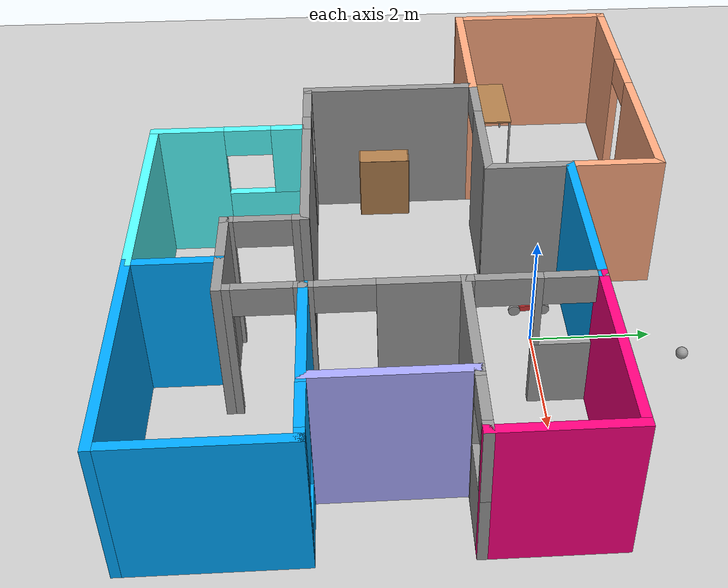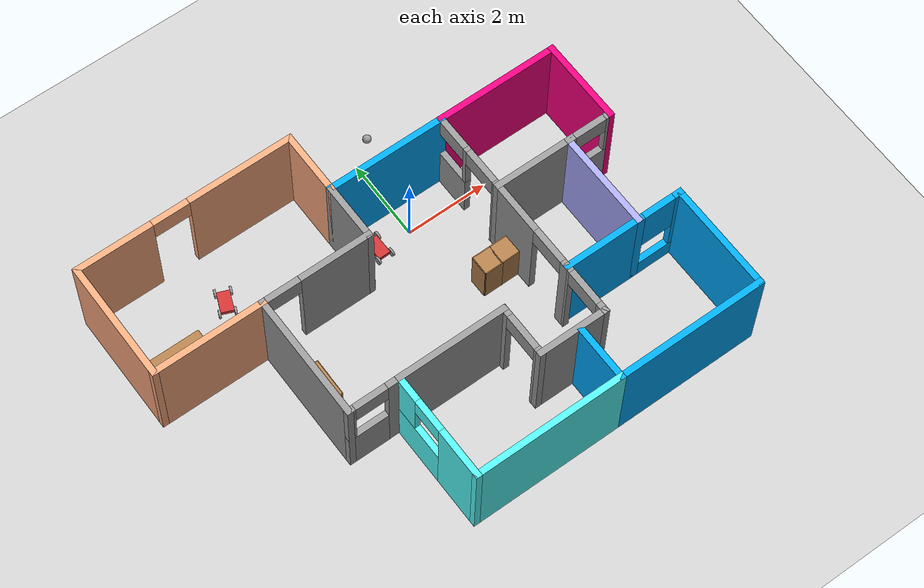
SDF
<sdf version="1.7">
 <world name="default">
  <plugin name="welcome" filename="libwelcome.so"/>
  <light name="sun" type="directional">
   <pose>0 0 10 0 -0 0</pose>
   <diffuse>0.8 0.8 0.8 1</diffuse>
   <specular>0.2 0.2 0.2 1</specular>
   <attenuation>
    <range>1000</range>
    <constant>0.9</constant>
    <linear>0.01</linear>
    <quadratic>0.001</quadratic>
   </attenuation>
   <direction>-0.5 0.1 -0.9</direction>
  </light>
  <model name="ground_plane">
   <static>1</static>
   <link name="link">
    <collision name="collision">
     <geometry><plane><normal>0 0 1</normal><size>100 100</size></plane></geometry>
     <surface>
      <contact><collide_bitmask>65535</collide_bitmask></contact>
      <friction><ode><mu>100</mu><mu2>50</mu2></ode></friction>
     </surface>
    </collision>
    <visual name="visual">
     <cast_shadows>0</cast_shadows>
     <geometry><plane><normal>0 0 1</normal><size>100 100</size></plane></geometry>
     <material>
      <script><uri>file://media/materials/scripts/gazebo.material</uri><name>Gazebo/Grey</name></script>
     </material>
    </visual>
   </link>
  </model>
  <gravity>0 0 -9.8</gravity>
  <magnetic_field>6e-06 2.3e-05 -4.2e-05</magnetic_field>
  <atmosphere type="adiabatic"/>
  <physics name="default_physics" default="0" type="ode">
   <max_step_size>0.001</max_step_size>
   <real_time_factor>1</real_time_factor>
   <real_time_update_rate>1000</real_time_update_rate>
  </physics>
  <scene><ambient>0.4 0.4 0.4 1</ambient><background>0.7 0.7 0.7 1</background><shadows>1</shadows></scene>
  <spherical_coordinates>
   <surface_model>EARTH_WGS84</surface_model>
   <latitude_deg>0</latitude_deg>
   <longitude_deg>0</longitude_deg>
   <elevation>0</elevation>
   <heading_deg>0</heading_deg>
  </spherical_coordinates>
  <model name="Building">
   <pose>-1.24556 -1.99914 0 0 -0 0</pose>
   <link name="Wall_0">
    <pose>-1.575 1.37479 0 0 -0 0</pose>
    <visual name="Wall_0_Visual_0">
     <pose>-1.35895 0 1.25 0 -0 0</pose>
     <geometry><box><size>0.0821 0.15 2.5</size></box></geometry>
     <material>
      <script><uri>file://media/materials/scripts/gazebo.material</uri><name>Gazebo/Grey</name></script>
      <ambient>1 1 1 1</ambient>
     </material>
     <meta><layer>0</layer></meta>
    </visual>
    <collision name="Wall_0_Collision_0">
     <geometry><box><size>0.0821 0.15 2.5</size></box></geometry>
     <pose>-1.35895 0 1.25 0 -0 0</pose>
    </collision>
    <visual name="Wall_0_Visual_1">
     <pose>0.49105 0 1.25 0 -0 0</pose>
     <geometry><box><size>1.8179 0.15 2.5</size></box></geometry>
     <material>
      <script><uri>file://media/materials/scripts/gazebo.material</uri><name>Gazebo/Grey</name></script>
      <ambient>1 1 1 1</ambient>
     </material>
     <meta><layer>0</layer></meta>
    </visual>
    <collision name="Wall_0_Collision_1">
     <geometry><box><size>1.8179 0.15 2.5</size></box></geometry>
     <pose>0.49105 0 1.25 0 -0 0</pose>
    </collision>
    <visual name="Wall_0_Visual_2">
     <pose>-0.8679 0 2.25 0 -0 0</pose>
     <geometry><box><size>0.9 0.15 0.5</size></box></geometry>
     <material>
      <script><uri>file://media/materials/scripts/gazebo.material</uri><name>Gazebo/Grey</name></script>
      <ambient>1 1 1 1</ambient>
     </material>
     <meta><layer>0</layer></meta>
    </visual>
    <collision name="Wall_0_Collision_2">
     <geometry><box><size>0.9 0.15 0.5</size></box></geometry>
     <pose>-0.8679 0 2.25 0 -0 0</pose>
    </collision>
   </link>
   <link name="Wall_1">
    <collision name="Wall_1_Collision">
     <geometry><box><size>1.5 0.15 2.5</size></box></geometry>
     <pose>0 0 1.25 0 -0 0</pose>
    </collision>
    <visual name="Wall_1_Visual">
     <pose>0 0 1.25 0 -0 0</pose>
     <geometry><box><size>1.5 0.15 2.5</size></box></geometry>
     <material>
      <script><uri>file://media/materials/scripts/gazebo.material</uri><name>Gazebo/Grey</name></script>
      <ambient>1 1 1 1</ambient>
     </material>
     <meta><layer>0</layer></meta>
    </visual>
    <pose>-0.25 2.04979 0 0 -0 1.5708</pose>
   </link>
   <link name="Wall_11">
    <collision name="Wall_11_Collision">
     <geometry><box><size>2 0.15 2.5</size></box></geometry>
     <pose>0 0 1.25 0 -0 0</pose>
    </collision>
    <visual name="Wall_11_Visual">
     <pose>0 0 1.25 0 -0 0</pose>
     <geometry><box><size>2 0.15 2.5</size></box></geometry>
     <material>
      <script><uri>file://media/materials/scripts/gazebo.material</uri><name>Gazebo/Grey</name></script>
      <ambient>0 0.666667 1 1</ambient>
     </material>
     <meta><layer>0</layer></meta>
    </visual>
    <pose>3.525 -1.62521 0 0 -0 0</pose>
   </link>
   <link name="Wall_12">
    <collision name="Wall_12_Collision">
     <geometry><box><size>2.5 0.15 2.5</size></box></geometry>
     <pose>0 0 1.25 0 -0 0</pose>
    </collision>
    <visual name="Wall_12_Visual">
     <pose>0 0 1.25 0 -0 0</pose>
     <geometry><box><size>2.5 0.15 2.5</size></box></geometry>
     <material>
      <script><uri>file://media/materials/scripts/gazebo.material</uri><name>Gazebo/Grey</name></script>
      <ambient>0.666667 0.666667 1 1</ambient>
     </material>
     <meta><layer>0</layer></meta>
    </visual>
    <pose>4.45 -0.450208 0 0 -0 1.5708</pose>
   </link>
   <link name="Wall_16">
    <pose>5 -1.62521 0 0 -0 0</pose>
    <visual name="Wall_16_Visual_0">
     <pose>-0.522443 0 1.25 0 -0 0</pose>
     <geometry><box><size>0.205115 0.15 2.5</size></box></geometry>
     <material>
      <script><uri>file://media/materials/scripts/gazebo.material</uri><name>Gazebo/Grey</name></script>
      <ambient>0 0.666667 1 1</ambient>
     </material>
     <meta><layer>0</layer></meta>
    </visual>
    <collision name="Wall_16_Collision_0">
     <geometry><box><size>0.205115 0.15 2.5</size></box></geometry>
     <pose>-0.522443 0 1.25 0 -0 0</pose>
    </collision>
    <visual name="Wall_16_Visual_1">
     <pose>0.102557 0 0.25 0 -0 0</pose>
     <geometry><box><size>1.04489 0.15 0.5</size></box></geometry>
     <material>
      <script><uri>file://media/materials/scripts/gazebo.material</uri><name>Gazebo/Grey</name></script>
      <ambient>0 0.666667 1 1</ambient>
     </material>
     <meta><layer>0</layer></meta>
    </visual>
    <collision name="Wall_16_Collision_1">
     <geometry><box><size>1.04489 0.15 0.5</size></box></geometry>
     <pose>0.102557 0 0.25 0 -0 0</pose>
    </collision>
    <visual name="Wall_16_Visual_2">
     <pose>0.502557 0 1.5 0 -0 0</pose>
     <geometry><box><size>0.244885 0.15 2</size></box></geometry>
     <material>
      <script><uri>file://media/materials/scripts/gazebo.material</uri><name>Gazebo/Grey</name></script>
      <ambient>0 0.666667 1 1</ambient>
     </material>
     <meta><layer>0</layer></meta>
    </visual>
    <collision name="Wall_16_Collision_2">
     <geometry><box><size>0.244885 0.15 2</size></box></geometry>
     <pose>0.502557 0 1.5 0 -0 0</pose>
    </collision>
    <visual name="Wall_16_Visual_3">
     <pose>-0.019885 0 1.9 0 -0 0</pose>
     <geometry><box><size>0.8 0.15 1.2</size></box></geometry>
     <material>
      <script><uri>file://media/materials/scripts/gazebo.material</uri><name>Gazebo/Grey</name></script>
      <ambient>0 0.666667 1 1</ambient>
     </material>
     <meta><layer>0</layer></meta>
    </visual>
    <collision name="Wall_16_Collision_3">
     <geometry><box><size>0.8 0.15 1.2</size></box></geometry>
     <pose>-0.019885 0 1.9 0 -0 0</pose>
    </collision>
   </link>
   <link name="Wall_17">
    <collision name="Wall_17_Collision">
     <geometry><box><size>2.75 0.15 2.5</size></box></geometry>
     <pose>0 0 1.25 0 -0 0</pose>
    </collision>
    <visual name="Wall_17_Visual">
     <pose>0 0 1.25 0 -0 0</pose>
     <geometry><box><size>2.75 0.15 2.5</size></box></geometry>
     <material>
      <script><uri>file://media/materials/scripts/gazebo.material</uri><name>Gazebo/Grey</name></script>
      <ambient>0 0.666667 1 1</ambient>
     </material>
     <meta><layer>0</layer></meta>
    </visual>
    <pose>5.55 -2.92521 0 0 0 -1.5708</pose>
   </link>
   <link name="Wall_24">
    <collision name="Wall_24_Collision">
     <geometry><box><size>2 0.15 2.5</size></box></geometry>
     <pose>0 0 1.25 0 -0 0</pose>
    </collision>
    <visual name="Wall_24_Visual">
     <pose>0 0 1.25 0 -0 0</pose>
     <geometry><box><size>2 0.15 2.5</size></box></geometry>
     <material>
      <script><uri>file://media/materials/scripts/gazebo.material</uri><name>Gazebo/Grey</name></script>
      <ambient>1 1 1 1</ambient>
     </material>
     <meta><layer>0</layer></meta>
    </visual>
    <pose>3.525 0.724792 0 0 -0 3.14159</pose>
   </link>
   <link name="Wall_26">
    <pose>5 0.724792 0 0 -0 0</pose>
    <visual name="Wall_26_Visual_0">
     <pose>-0.511581 0 1.25 0 -0 0</pose>
     <geometry><box><size>0.226838 0.15 2.5</size></box></geometry>
     <material>
      <script><uri>file://media/materials/scripts/gazebo.material</uri><name>Gazebo/Grey</name></script>
      <ambient>1 1 1 1</ambient>
     </material>
     <meta><layer>0</layer></meta>
    </visual>
    <collision name="Wall_26_Collision_0">
     <geometry><box><size>0.226838 0.15 2.5</size></box></geometry>
     <pose>-0.511581 0 1.25 0 -0 0</pose>
    </collision>
    <visual name="Wall_26_Visual_1">
     <pose>0.113419 0 0.6 0 -0 0</pose>
     <geometry><box><size>1.02316 0.15 1.2</size></box></geometry>
     <material>
      <script><uri>file://media/materials/scripts/gazebo.material</uri><name>Gazebo/Grey</name></script>
      <ambient>1 1 1 1</ambient>
     </material>
     <meta><layer>0</layer></meta>
    </visual>
    <collision name="Wall_26_Collision_1">
     <geometry><box><size>1.02316 0.15 1.2</size></box></geometry>
     <pose>0.113419 0 0.6 0 -0 0</pose>
    </collision>
    <visual name="Wall_26_Visual_2">
     <pose>0.513419 0 1.85 0 -0 0</pose>
     <geometry><box><size>0.223162 0.15 1.3</size></box></geometry>
     <material>
      <script><uri>file://media/materials/scripts/gazebo.material</uri><name>Gazebo/Grey</name></script>
      <ambient>1 1 1 1</ambient>
     </material>
     <meta><layer>0</layer></meta>
    </visual>
    <collision name="Wall_26_Collision_2">
     <geometry><box><size>0.223162 0.15 1.3</size></box></geometry>
     <pose>0.513419 0 1.85 0 -0 0</pose>
    </collision>
    <visual name="Wall_26_Visual_3">
     <pose>0.001838 0 2.25 0 -0 0</pose>
     <geometry><box><size>0.8 0.15 0.5</size></box></geometry>
     <material>
      <script><uri>file://media/materials/scripts/gazebo.material</uri><name>Gazebo/Grey</name></script>
      <ambient>1 1 1 1</ambient>
     </material>
     <meta><layer>0</layer></meta>
    </visual>
    <collision name="Wall_26_Collision_3">
     <geometry><box><size>0.8 0.15 0.5</size></box></geometry>
     <pose>0.001838 0 2.25 0 -0 0</pose>
    </collision>
   </link>
   <link name="Wall_29">
    <collision name="Wall_29_Collision">
     <geometry><box><size>3.1 0.15 2.5</size></box></geometry>
     <pose>0 0 1.25 0 -0 0</pose>
    </collision>
    <visual name="Wall_29_Visual">
     <pose>0 0 1.25 0 -0 0</pose>
     <geometry><box><size>3.1 0.15 2.5</size></box></geometry>
     <material>
      <script><uri>file://media/materials/scripts/gazebo.material</uri><name>Gazebo/Grey</name></script>
      <ambient>1 0 0.498039 1</ambient>
     </material>
     <meta><layer>0</layer></meta>
    </visual>
    <pose>4.075 2.72479 0 0 -0 0</pose>
   </link>
   <link name="Wall_3">
    <collision name="Wall_3_Collision">
     <geometry><box><size>3 0.15 2.5</size></box></geometry>
     <pose>0 0 1.25 0 -0 0</pose>
    </collision>
    <visual name="Wall_3_Visual">
     <pose>0 0 1.25 0 -0 0</pose>
     <geometry><box><size>3 0.15 2.5</size></box></geometry>
     <material>
      <script><uri>file://media/materials/scripts/gazebo.material</uri><name>Gazebo/Grey</name></script>
      <ambient>0 0.666667 1 1</ambient>
     </material>
     <meta><layer>0</layer></meta>
    </visual>
    <pose>1.175 2.72479 0 0 -0 0</pose>
   </link>
   <link name="Wall_31">
    <collision name="Wall_31_Collision">
     <geometry><box><size>2.15016 0.15 2.5</size></box></geometry>
     <pose>0 0 1.25 0 -0 0</pose>
    </collision>
    <visual name="Wall_31_Visual">
     <pose>0 0 1.25 0 -0 0</pose>
     <geometry><box><size>2.15016 0.15 2.5</size></box></geometry>
     <material>
      <script><uri>file://media/materials/scripts/gazebo.material</uri><name>Gazebo/Grey</name></script>
      <ambient>1 0 0.498039 1</ambient>
     </material>
     <meta><layer>0</layer></meta>
    </visual>
    <pose>5.55 1.72479 0 0 0 -1.5708</pose>
   </link>
   <link name="Wall_4">
    <pose>2.6 0.549792 0 0 0 -1.5708</pose>
    <visual name="Wall_4_Visual_0">
     <pose>-2.17703 0 1.25 0 -0 0</pose>
     <geometry><box><size>0.145935 0.15 2.5</size></box></geometry>
     <material>
      <script><uri>file://media/materials/scripts/gazebo.material</uri><name>Gazebo/Grey</name></script>
      <ambient>1 1 1 1</ambient>
     </material>
     <meta><layer>0</layer></meta>
    </visual>
    <collision name="Wall_4_Collision_0">
     <geometry><box><size>0.145935 0.15 2.5</size></box></geometry>
     <pose>-2.17703 0 1.25 0 -0 0</pose>
    </collision>
    <visual name="Wall_4_Visual_1">
     <pose>0.412483 0 1.25 0 -0 0</pose>
     <geometry><box><size>1.42285 0.15 2.5</size></box></geometry>
     <material>
      <script><uri>file://media/materials/scripts/gazebo.material</uri><name>Gazebo/Grey</name></script>
      <ambient>1 1 1 1</ambient>
     </material>
     <meta><layer>0</layer></meta>
    </visual>
    <collision name="Wall_4_Collision_1">
     <geometry><box><size>1.42285 0.15 2.5</size></box></geometry>
     <pose>0.412483 0 1.25 0 -0 0</pose>
    </collision>
    <visual name="Wall_4_Visual_2">
     <pose>2.13695 0 1.25 0 -0 0</pose>
     <geometry><box><size>0.226091 0.15 2.5</size></box></geometry>
     <material>
      <script><uri>file://media/materials/scripts/gazebo.material</uri><name>Gazebo/Grey</name></script>
      <ambient>1 1 1 1</ambient>
     </material>
     <meta><layer>0</layer></meta>
    </visual>
    <collision name="Wall_4_Collision_2">
     <geometry><box><size>0.226091 0.15 2.5</size></box></geometry>
     <pose>2.13695 0 1.25 0 -0 0</pose>
    </collision>
    <visual name="Wall_4_Visual_3">
     <pose>-1.65151 0 0.6 0 -0 0</pose>
     <geometry><box><size>0.905122 0.15 1.2</size></box></geometry>
     <material>
      <script><uri>file://media/materials/scripts/gazebo.material</uri><name>Gazebo/Grey</name></script>
      <ambient>1 1 1 1</ambient>
     </material>
     <meta><layer>0</layer></meta>
    </visual>
    <collision name="Wall_4_Collision_3">
     <geometry><box><size>0.905122 0.15 1.2</size></box></geometry>
     <pose>-1.65151 0 0.6 0 -0 0</pose>
    </collision>
    <visual name="Wall_4_Visual_4">
     <pose>-1.25151 0 1.85 0 -0 0</pose>
     <geometry><box><size>0.105122 0.15 1.3</size></box></geometry>
     <material>
      <script><uri>file://media/materials/scripts/gazebo.material</uri><name>Gazebo/Grey</name></script>
      <ambient>1 1 1 1</ambient>
     </material>
     <meta><layer>0</layer></meta>
    </visual>
    <collision name="Wall_4_Collision_4">
     <geometry><box><size>0.105122 0.15 1.3</size></box></geometry>
     <pose>-1.25151 0 1.85 0 -0 0</pose>
    </collision>
    <visual name="Wall_4_Visual_5">
     <pose>1.57391 0 2.25 0 -0 0</pose>
     <geometry><box><size>0.9 0.15 0.5</size></box></geometry>
     <material>
      <script><uri>file://media/materials/scripts/gazebo.material</uri><name>Gazebo/Grey</name></script>
      <ambient>1 1 1 1</ambient>
     </material>
     <meta><layer>0</layer></meta>
    </visual>
    <collision name="Wall_4_Collision_5">
     <geometry><box><size>0.9 0.15 0.5</size></box></geometry>
     <pose>1.57391 0 2.25 0 -0 0</pose>
    </collision>
    <visual name="Wall_4_Visual_6">
     <pose>-0.748944 0 2.25 0 -0 0</pose>
     <geometry><box><size>0.9 0.15 0.5</size></box></geometry>
     <material>
      <script><uri>file://media/materials/scripts/gazebo.material</uri><name>Gazebo/Grey</name></script>
      <ambient>1 1 1 1</ambient>
     </material>
     <meta><layer>0</layer></meta>
    </visual>
    <collision name="Wall_4_Collision_6">
     <geometry><box><size>0.9 0.15 0.5</size></box></geometry>
     <pose>-0.748944 0 2.25 0 -0 0</pose>
    </collision>
    <visual name="Wall_4_Visual_7">
     <pose>-1.70406 0 2.25 0 -0 0</pose>
     <geometry><box><size>0.8 0.15 0.5</size></box></geometry>
     <material>
      <script><uri>file://media/materials/scripts/gazebo.material</uri><name>Gazebo/Grey</name></script>
      <ambient>1 1 1 1</ambient>
     </material>
     <meta><layer>0</layer></meta>
    </visual>
    <collision name="Wall_4_Collision_7">
     <geometry><box><size>0.8 0.15 0.5</size></box></geometry>
     <pose>-1.70406 0 2.25 0 -0 0</pose>
    </collision>
   </link>
   <link name="Wall_41">
    <pose>2.6 -2.24421 0 0 0 -1.5708</pose>
    <visual name="Wall_41_Visual_0">
     <pose>-0.586201 0 1.25 0 -0 0</pose>
     <geometry><box><size>0.21618 0.15 2.5</size></box></geometry>
     <material>
      <script><uri>file://media/materials/scripts/gazebo.material</uri><name>Gazebo/Grey</name></script>
      <ambient>1 1 1 1</ambient>
     </material>
     <meta><layer>0</layer></meta>
    </visual>
    <collision name="Wall_41_Collision_0">
     <geometry><box><size>0.21618 0.15 2.5</size></box></geometry>
     <pose>-0.586201 0 1.25 0 -0 0</pose>
    </collision>
    <visual name="Wall_41_Visual_1">
     <pose>0.55809 0 1.25 0 -0 0</pose>
     <geometry><box><size>0.272401 0.15 2.5</size></box></geometry>
     <material>
      <script><uri>file://media/materials/scripts/gazebo.material</uri><name>Gazebo/Grey</name></script>
      <ambient>1 1 1 1</ambient>
     </material>
     <meta><layer>0</layer></meta>
    </visual>
    <collision name="Wall_41_Collision_1">
     <geometry><box><size>0.272401 0.15 2.5</size></box></geometry>
     <pose>0.55809 0 1.25 0 -0 0</pose>
    </collision>
    <visual name="Wall_41_Visual_2">
     <pose>-0.028111 0 2.25 0 -0 0</pose>
     <geometry><box><size>0.9 0.15 0.5</size></box></geometry>
     <material>
      <script><uri>file://media/materials/scripts/gazebo.material</uri><name>Gazebo/Grey</name></script>
      <ambient>1 1 1 1</ambient>
     </material>
     <meta><layer>0</layer></meta>
    </visual>
    <collision name="Wall_41_Collision_2">
     <geometry><box><size>0.9 0.15 0.5</size></box></geometry>
     <pose>-0.028111 0 2.25 0 -0 0</pose>
    </collision>
   </link>
   <link name="Wall_42">
    <collision name="Wall_42_Collision">
     <geometry><box><size>1.78 0.15 2.5</size></box></geometry>
     <pose>0 0 1.25 0 -0 0</pose>
    </collision>
    <visual name="Wall_42_Visual">
     <pose>0 0 1.25 0 -0 0</pose>
     <geometry><box><size>1.78 0.15 2.5</size></box></geometry>
     <material>
      <script><uri>file://media/materials/scripts/gazebo.material</uri><name>Gazebo/Grey</name></script>
      <ambient>1 1 1 1</ambient>
     </material>
     <meta><layer>0</layer></meta>
    </visual>
    <pose>1.785 -2.86321 0 0 -0 3.14159</pose>
   </link>
   <link name="Wall_43">
    <pose>0.97 -2.24421 0 0 -0 1.5708</pose>
    <visual name="Wall_43_Visual_0">
     <pose>-0.58591 0 1.25 0 -0 0</pose>
     <geometry><box><size>0.216762 0.15 2.5</size></box></geometry>
     <material>
      <script><uri>file://media/materials/scripts/gazebo.material</uri><name>Gazebo/Grey</name></script>
      <ambient>1 1 1 1</ambient>
     </material>
     <meta><layer>0</layer></meta>
    </visual>
    <collision name="Wall_43_Collision_0">
     <geometry><box><size>0.216762 0.15 2.5</size></box></geometry>
     <pose>-0.58591 0 1.25 0 -0 0</pose>
    </collision>
    <visual name="Wall_43_Visual_1">
     <pose>0.558381 0 1.25 0 -0 0</pose>
     <geometry><box><size>0.271819 0.15 2.5</size></box></geometry>
     <material>
      <script><uri>file://media/materials/scripts/gazebo.material</uri><name>Gazebo/Grey</name></script>
      <ambient>1 1 1 1</ambient>
     </material>
     <meta><layer>0</layer></meta>
    </visual>
    <collision name="Wall_43_Collision_1">
     <geometry><box><size>0.271819 0.15 2.5</size></box></geometry>
     <pose>0.558381 0 1.25 0 -0 0</pose>
    </collision>
    <visual name="Wall_43_Visual_2">
     <pose>-0.027529 0 2.25 0 -0 0</pose>
     <geometry><box><size>0.9 0.15 0.5</size></box></geometry>
     <material>
      <script><uri>file://media/materials/scripts/gazebo.material</uri><name>Gazebo/Grey</name></script>
      <ambient>1 1 1 1</ambient>
     </material>
     <meta><layer>0</layer></meta>
    </visual>
    <collision name="Wall_43_Collision_2">
     <geometry><box><size>0.9 0.15 0.5</size></box></geometry>
     <pose>-0.027529 0 2.25 0 -0 0</pose>
    </collision>
   </link>
   <link name="Wall_46">
    <collision name="Wall_46_Collision">
     <geometry><box><size>3.75 0.15 2.5</size></box></geometry>
     <pose>0 0 1.25 0 -0 0</pose>
    </collision>
    <visual name="Wall_46_Visual">
     <pose>0 0 1.25 0 -0 0</pose>
     <geometry><box><size>3.75 0.15 2.5</size></box></geometry>
     <material>
      <script><uri>file://media/materials/scripts/gazebo.material</uri><name>Gazebo/Grey</name></script>
      <ambient>0 0.666667 1 1</ambient>
     </material>
     <meta><layer>0</layer></meta>
    </visual>
    <pose>3.75 -4.22521 0 0 -0 3.14159</pose>
   </link>
   <link name="Wall_47">
    <collision name="Wall_47_Collision">
     <geometry><box><size>1.5 0.15 2.5</size></box></geometry>
     <pose>0 0 1.25 0 -0 0</pose>
    </collision>
    <visual name="Wall_47_Visual">
     <pose>0 0 1.25 0 -0 0</pose>
     <geometry><box><size>1.5 0.15 2.5</size></box></geometry>
     <material>
      <script><uri>file://media/materials/scripts/gazebo.material</uri><name>Gazebo/Grey</name></script>
      <ambient>0 0.666667 1 1</ambient>
     </material>
     <meta><layer>0</layer></meta>
    </visual>
    <pose>1.95 -3.55021 0 0 -0 1.5708</pose>
   </link>
   <link name="Wall_49">
    <collision name="Wall_49_Collision">
     <geometry><box><size>3.75 0.15 2.5</size></box></geometry>
     <pose>0 0 1.25 0 -0 0</pose>
    </collision>
    <visual name="Wall_49_Visual">
     <pose>0 0 1.25 0 -0 0</pose>
     <geometry><box><size>3.75 0.15 2.5</size></box></geometry>
     <material>
      <script><uri>file://media/materials/scripts/gazebo.material</uri><name>Gazebo/Grey</name></script>
      <ambient>0.333333 1 1 1</ambient>
     </material>
     <meta><layer>0</layer></meta>
    </visual>
    <pose>0.15 -4.22521 0 0 -0 3.14159</pose>
   </link>
   <link name="Wall_51">
    <pose>-1.65 -2.92521 0 0 -0 1.5708</pose>
    <visual name="Wall_51_Visual_0">
     <pose>-0.747196 0 1.25 0 -0 0</pose>
     <geometry><box><size>1.25561 0.15 2.5</size></box></geometry>
     <material>
      <script><uri>file://media/materials/scripts/gazebo.material</uri><name>Gazebo/Grey</name></script>
      <ambient>0.333333 1 1 1</ambient>
     </material>
     <meta><layer>0</layer></meta>
    </visual>
    <collision name="Wall_51_Collision_0">
     <geometry><box><size>1.25561 0.15 2.5</size></box></geometry>
     <pose>-0.747196 0 1.25 0 -0 0</pose>
    </collision>
    <visual name="Wall_51_Visual_1">
     <pose>0.627804 0 0.6 0 -0 0</pose>
     <geometry><box><size>1.49439 0.15 1.2</size></box></geometry>
     <material>
      <script><uri>file://media/materials/scripts/gazebo.material</uri><name>Gazebo/Grey</name></script>
      <ambient>0.333333 1 1 1</ambient>
     </material>
     <meta><layer>0</layer></meta>
    </visual>
    <collision name="Wall_51_Collision_1">
     <geometry><box><size>1.49439 0.15 1.2</size></box></geometry>
     <pose>0.627804 0 0.6 0 -0 0</pose>
    </collision>
    <visual name="Wall_51_Visual_2">
     <pose>1.0278 0 1.85 0 -0 0</pose>
     <geometry><box><size>0.694393 0.15 1.3</size></box></geometry>
     <material>
      <script><uri>file://media/materials/scripts/gazebo.material</uri><name>Gazebo/Grey</name></script>
      <ambient>0.333333 1 1 1</ambient>
     </material>
     <meta><layer>0</layer></meta>
    </visual>
    <collision name="Wall_51_Collision_2">
     <geometry><box><size>0.694393 0.15 1.3</size></box></geometry>
     <pose>1.0278 0 1.85 0 -0 0</pose>
    </collision>
    <visual name="Wall_51_Visual_3">
     <pose>0.280607 0 2.25 0 -0 0</pose>
     <geometry><box><size>0.8 0.15 0.5</size></box></geometry>
     <material>
      <script><uri>file://media/materials/scripts/gazebo.material</uri><name>Gazebo/Grey</name></script>
      <ambient>0.333333 1 1 1</ambient>
     </material>
     <meta><layer>0</layer></meta>
    </visual>
    <collision name="Wall_51_Collision_3">
     <geometry><box><size>0.8 0.15 0.5</size></box></geometry>
     <pose>0.280607 0 2.25 0 -0 0</pose>
    </collision>
   </link>
   <link name="Wall_52">
    <collision name="Wall_52_Collision">
     <geometry><box><size>2.77 0.15 2.5</size></box></geometry>
     <pose>0 0 1.25 0 -0 0</pose>
    </collision>
    <visual name="Wall_52_Visual">
     <pose>0 0 1.25 0 -0 0</pose>
     <geometry><box><size>2.77 0.15 2.5</size></box></geometry>
     <material>
      <script><uri>file://media/materials/scripts/gazebo.material</uri><name>Gazebo/Grey</name></script>
      <ambient>1 1 1 1</ambient>
     </material>
     <meta><layer>0</layer></meta>
    </visual>
    <pose>-0.34 -1.62521 0 0 -0 0</pose>
   </link>
   <link name="Wall_54">
    <pose>-2.275 -1.62521 0 0 -0 3.14159</pose>
    <visual name="Wall_54_Visual_0">
     <pose>-0.501383 0 1.25 0 -0 0</pose>
     <geometry><box><size>0.397234 0.15 2.5</size></box></geometry>
     <material>
      <script><uri>file://media/materials/scripts/gazebo.material</uri><name>Gazebo/Grey</name></script>
      <ambient>1 1 1 1</ambient>
     </material>
     <meta><layer>0</layer></meta>
    </visual>
    <collision name="Wall_54_Collision_0">
     <geometry><box><size>0.397234 0.15 2.5</size></box></geometry>
     <pose>-0.501383 0 1.25 0 -0 0</pose>
    </collision>
    <visual name="Wall_54_Visual_1">
     <pose>0.198617 0 0.6 0 -0 0</pose>
     <geometry><box><size>1.00277 0.15 1.2</size></box></geometry>
     <material>
      <script><uri>file://media/materials/scripts/gazebo.material</uri><name>Gazebo/Grey</name></script>
      <ambient>1 1 1 1</ambient>
     </material>
     <meta><layer>0</layer></meta>
    </visual>
    <collision name="Wall_54_Collision_1">
     <geometry><box><size>1.00277 0.15 1.2</size></box></geometry>
     <pose>0.198617 0 0.6 0 -0 0</pose>
    </collision>
    <visual name="Wall_54_Visual_2">
     <pose>0.598617 0 1.85 0 -0 0</pose>
     <geometry><box><size>0.202766 0.15 1.3</size></box></geometry>
     <material>
      <script><uri>file://media/materials/scripts/gazebo.material</uri><name>Gazebo/Grey</name></script>
      <ambient>1 1 1 1</ambient>
     </material>
     <meta><layer>0</layer></meta>
    </visual>
    <collision name="Wall_54_Collision_2">
     <geometry><box><size>0.202766 0.15 1.3</size></box></geometry>
     <pose>0.598617 0 1.85 0 -0 0</pose>
    </collision>
    <visual name="Wall_54_Visual_3">
     <pose>0.097234 0 2.25 0 -0 0</pose>
     <geometry><box><size>0.8 0.15 0.5</size></box></geometry>
     <material>
      <script><uri>file://media/materials/scripts/gazebo.material</uri><name>Gazebo/Grey</name></script>
      <ambient>1 1 1 1</ambient>
     </material>
     <meta><layer>0</layer></meta>
    </visual>
    <collision name="Wall_54_Collision_3">
     <geometry><box><size>0.8 0.15 0.5</size></box></geometry>
     <pose>0.097234 0 2.25 0 -0 0</pose>
    </collision>
   </link>
   <link name="Wall_55">
    <collision name="Wall_55_Collision">
     <geometry><box><size>3.15042 0.15 2.5</size></box></geometry>
     <pose>0 0 1.25 0 -0 0</pose>
    </collision>
    <visual name="Wall_55_Visual">
     <pose>0 0 1.25 0 -0 0</pose>
     <geometry><box><size>3.15042 0.15 2.5</size></box></geometry>
     <material>
      <script><uri>file://media/materials/scripts/gazebo.material</uri><name>Gazebo/Grey</name></script>
      <ambient>1 1 1 1</ambient>
     </material>
     <meta><layer>0</layer></meta>
    </visual>
    <pose>-2.9 -0.125208 0 0 -0 1.5708</pose>
   </link>
   <link name="Wall_57">
    <collision name="Wall_57_Collision">
     <geometry><box><size>2.8 0.15 2.5</size></box></geometry>
     <pose>0 0 1.25 0 -0 0</pose>
    </collision>
    <visual name="Wall_57_Visual">
     <pose>0 0 1.25 0 -0 0</pose>
     <geometry><box><size>2.8 0.15 2.5</size></box></geometry>
     <material>
      <script><uri>file://media/materials/scripts/gazebo.material</uri><name>Gazebo/Grey</name></script>
      <ambient>1 0.666667 0.498039 1</ambient>
     </material>
     <meta><layer>0</layer></meta>
    </visual>
    <pose>-4.225 1.37479 0 0 -0 3.14159</pose>
   </link>
   <link name="Wall_60">
    <collision name="Wall_60_Collision">
     <geometry><box><size>3 0.15 2.5</size></box></geometry>
     <pose>0 0 1.25 0 -0 0</pose>
    </collision>
    <visual name="Wall_60_Visual">
     <pose>0 0 1.25 0 -0 0</pose>
     <geometry><box><size>3 0.15 2.5</size></box></geometry>
     <material>
      <script><uri>file://media/materials/scripts/gazebo.material</uri><name>Gazebo/Grey</name></script>
      <ambient>1 0.666667 0.498039 1</ambient>
     </material>
     <meta><layer>0</layer></meta>
    </visual>
    <pose>-5.55 2.79979 0 0 -0 1.5708</pose>
   </link>
   <link name="Wall_62">
    <pose>-2.9 4.22479 0 0 -0 0</pose>
    <visual name="Wall_62_Visual_0">
     <pose>-1.77004 0 1.25 0 -0 0</pose>
     <geometry><box><size>1.90993 0.15 2.5</size></box></geometry>
     <material>
      <script><uri>file://media/materials/scripts/gazebo.material</uri><name>Gazebo/Grey</name></script>
      <ambient>1 0.666667 0.498039 1</ambient>
     </material>
     <meta><layer>0</layer></meta>
    </visual>
    <collision name="Wall_62_Collision_0">
     <geometry><box><size>1.90993 0.15 2.5</size></box></geometry>
     <pose>-1.77004 0 1.25 0 -0 0</pose>
    </collision>
    <visual name="Wall_62_Visual_1">
     <pose>1.40496 0 1.25 0 -0 0</pose>
     <geometry><box><size>2.64007 0.15 2.5</size></box></geometry>
     <material>
      <script><uri>file://media/materials/scripts/gazebo.material</uri><name>Gazebo/Grey</name></script>
      <ambient>1 0.666667 0.498039 1</ambient>
     </material>
     <meta><layer>0</layer></meta>
    </visual>
    <collision name="Wall_62_Collision_1">
     <geometry><box><size>2.64007 0.15 2.5</size></box></geometry>
     <pose>1.40496 0 1.25 0 -0 0</pose>
    </collision>
    <visual name="Wall_62_Visual_2">
     <pose>-0.365072 0 2.25 0 -0 0</pose>
     <geometry><box><size>0.9 0.15 0.5</size></box></geometry>
     <material>
      <script><uri>file://media/materials/scripts/gazebo.material</uri><name>Gazebo/Grey</name></script>
      <ambient>1 0.666667 0.498039 1</ambient>
     </material>
     <meta><layer>0</layer></meta>
    </visual>
    <collision name="Wall_62_Collision_2">
     <geometry><box><size>0.9 0.15 0.5</size></box></geometry>
     <pose>-0.365072 0 2.25 0 -0 0</pose>
    </collision>
   </link>
   <link name="Wall_63">
    <collision name="Wall_63_Collision">
     <geometry><box><size>1.65083 0.15 2.5</size></box></geometry>
     <pose>0 0 1.25 0 -0 0</pose>
    </collision>
    <visual name="Wall_63_Visual">
     <pose>0 0 1.25 0 -0 0</pose>
     <geometry><box><size>1.65083 0.15 2.5</size></box></geometry>
     <material>
      <script><uri>file://media/materials/scripts/gazebo.material</uri><name>Gazebo/Grey</name></script>
      <ambient>1 0.666667 0.498039 1</ambient>
     </material>
     <meta><layer>0</layer></meta>
    </visual>
    <pose>-0.25 3.47479 0 0 0 -1.5708</pose>
   </link>
   <static>1</static>
  </model>
  <model name="bookshelf">
   <static>1</static>
   <link name="link">
    <inertial><mass>1</mass></inertial>
    <collision name="back">
     <pose>0 0.005 0.6 0 -0 0</pose>
     <geometry><box><size>0.9 0.01 1.2</size></box></geometry>
    </collision>
    <visual name="visual1">
     <pose>0 0.005 0.6 0 -0 0</pose>
     <geometry><box><size>0.9 0.01 1.2</size></box></geometry>
     <material>
      <script><uri>file://media/materials/scripts/gazebo.material</uri><name>Gazebo/Wood</name></script>
     </material>
    </visual>
    <collision name="left_side">
     <pose>0.45 -0.195 0.6 0 -0 0</pose>
     <geometry><box><size>0.02 0.4 1.2</size></box></geometry>
    </collision>
    <visual name="visual2">
     <pose>0.45 -0.195 0.6 0 -0 0</pose>
     <geometry><box><size>0.02 0.4 1.2</size></box></geometry>
     <material>
      <script><uri>file://media/materials/scripts/gazebo.material</uri><name>Gazebo/Wood</name></script>
     </material>
    </visual>
    <collision name="right_side">
     <pose>-0.45 -0.195 0.6 0 -0 0</pose>
     <geometry><box><size>0.02 0.4 1.2</size></box></geometry>
    </collision>
    <visual name="visual3">
     <pose>-0.45 -0.195 0.6 0 -0 0</pose>
     <geometry><box><size>0.02 0.4 1.2</size></box></geometry>
     <material>
      <script><uri>file://media/materials/scripts/gazebo.material</uri><name>Gazebo/Wood</name></script>
     </material>
    </visual>
    <collision name="bottom">
     <pose>0 -0.195 0.03 0 -0 0</pose>
     <geometry><box><size>0.88 0.4 0.06</size></box></geometry>
    </collision>
    <visual name="visual4">
     <pose>0 -0.195 0.03 0 -0 0</pose>
     <geometry><box><size>0.88 0.4 0.06</size></box></geometry>
     <material>
      <script><uri>file://media/materials/scripts/gazebo.material</uri><name>Gazebo/Wood</name></script>
     </material>
    </visual>
    <collision name="top">
     <pose>0 -0.195 1.19 0 -0 0</pose>
     <geometry><box><size>0.88 0.4 0.02</size></box></geometry>
    </collision>
    <visual name="visual5">
     <pose>0 -0.195 1.19 0 -0 0</pose>
     <geometry><box><size>0.88 0.4 0.02</size></box></geometry>
     <material>
      <script><uri>file://media/materials/scripts/gazebo.material</uri><name>Gazebo/Wood</name></script>
     </material>
    </visual>
    <collision name="low_shelf">
     <pose>0 -0.195 0.43 0 -0 0</pose>
     <geometry><box><size>0.88 0.4 0.02</size></box></geometry>
    </collision>
    <visual name="visual6">
     <pose>0 -0.195 0.43 0 -0 0</pose>
     <geometry><box><size>0.88 0.4 0.02</size></box></geometry>
     <material>
      <script><uri>file://media/materials/scripts/gazebo.material</uri><name>Gazebo/Wood</name></script>
     </material>
    </visual>
    <collision name="high_shelf">
     <pose>0 -0.195 0.8 0 -0 0</pose>
     <geometry><box><size>0.88 0.4 0.02</size></box></geometry>
    </collision>
    <visual name="visual7">
     <pose>0 -0.195 0.8 0 -0 0</pose>
     <geometry><box><size>0.88 0.4 0.02</size></box></geometry>
     <material>
      <script><uri>file://media/materials/scripts/gazebo.material</uri><name>Gazebo/Wood</name></script>
     </material>
    </visual>
   </link>
   <pose>-3.69168 -2.27488 0 0 -0 -1.58089</pose>
  </model>
  <model name="Robot4Wheels">
   <link name="link_0">
    <pose>-0 -0 -2.4e-05 0 -0 0</pose>
    <inertial>
     <mass>1</mass>
     <inertia>
      <ixx>0.166667</ixx>
      <ixy>0</ixy>
      <ixz>0</ixz>
      <iyy>0.166667</iyy>
      <iyz>0</iyz>
      <izz>0.166667</izz>
     </inertia>
    </inertial>
    <visual name="visual">
     <geometry><box><size>0.5 0.3 0.1</size></box></geometry>
     <material>
      <lighting>1</lighting>
      <script><uri>file://media/materials/scripts/gazebo.material</uri><name>Gazebo/Grey</name></script>
      <shader type="pixel"><normal_map>__default__</normal_map></shader>
      <ambient>0.8 0.2 0.1 1</ambient>
      <diffuse>0.8 0.2 0.2 1</diffuse>
      <specular>0.01 0.01 0.01 1</specular>
      <emissive>0 0 0 1</emissive>
     </material>
    </visual>
    <collision name="collision">
     <geometry><box><size>0.5 0.3 0.1</size></box></geometry>
     <surface>
      <friction>
       <ode><mu>1</mu><mu2>1</mu2><fdir1>0 0 0</fdir1><slip1>0</slip1><slip2>0</slip2></ode>
       <torsional>
        <coefficient>1</coefficient>
        <patch_radius>0</patch_radius>
        <surface_radius>0</surface_radius>
        <use_patch_radius>1</use_patch_radius>
        <ode><slip>0</slip></ode>
       </torsional>
      </friction>
      <bounce><restitution_coefficient>0</restitution_coefficient><threshold>1e+06</threshold></bounce>
      <contact>
       <collide_without_contact>0</collide_without_contact>
       <collide_without_contact_bitmask>1</collide_without_contact_bitmask>
       <collide_bitmask>1</collide_bitmask>
       <ode>
        <soft_cfm>0</soft_cfm>
        <soft_erp>0.2</soft_erp>
        <kp>1e+13</kp>
        <kd>1</kd>
        <max_vel>0.01</max_vel>
        <min_depth>0</min_depth>
       </ode>
       <bullet>
        <split_impulse>1</split_impulse>
        <split_impulse_penetration_threshold>-0.01</split_impulse_penetration_threshold>
        <soft_cfm>0</soft_cfm>
        <soft_erp>0.2</soft_erp>
        <kp>1e+13</kp>
        <kd>1</kd>
       </bullet>
      </contact>
     </surface>
    </collision>
   </link>
   <link name="link_1">
    <pose>-0.25 -0.175014 6e-06 1.5707 -0 0</pose>
    <inertial>
     <mass>1</mass>
     <inertia><ixx>0.145833</ixx><ixy>0</ixy><ixz>0</ixz><iyy>0.145833</iyy><iyz>0</iyz><izz>0.125</izz></inertia>
    </inertial>
    <visual name="visual">
     <geometry><cylinder><radius>0.1</radius><length>0.05</length></cylinder></geometry>
     <material>
      <lighting>1</lighting>
      <script><uri>file://media/materials/scripts/gazebo.material</uri><name>Gazebo/Grey</name></script>
      <shader type="pixel"><normal_map>__default__</normal_map></shader>
      <ambient>0.3 0.3 0.3 1</ambient>
      <diffuse>0.7 0.7 0.7 1</diffuse>
      <specular>0.01 0.01 0.01 1</specular>
      <emissive>0 0 0 1</emissive>
     </material>
    </visual>
    <collision name="collision">
     <geometry><cylinder><radius>0.1</radius><length>0.05</length></cylinder></geometry>
     <surface>
      <friction>
       <ode><mu>1</mu><mu2>1</mu2><fdir1>0 0 0</fdir1><slip1>0</slip1><slip2>0</slip2></ode>
       <torsional>
        <coefficient>1</coefficient>
        <patch_radius>0</patch_radius>
        <surface_radius>0</surface_radius>
        <use_patch_radius>1</use_patch_radius>
        <ode><slip>0</slip></ode>
       </torsional>
      </friction>
      <bounce><restitution_coefficient>0</restitution_coefficient><threshold>1e+06</threshold></bounce>
      <contact>
       <collide_without_contact>0</collide_without_contact>
       <collide_without_contact_bitmask>1</collide_without_contact_bitmask>
       <collide_bitmask>1</collide_bitmask>
       <ode>
        <soft_cfm>0</soft_cfm>
        <soft_erp>0.2</soft_erp>
        <kp>1e+13</kp>
        <kd>1</kd>
        <max_vel>0.01</max_vel>
        <min_depth>0</min_depth>
       </ode>
       <bullet>
        <split_impulse>1</split_impulse>
        <split_impulse_penetration_threshold>-0.01</split_impulse_penetration_threshold>
        <soft_cfm>0</soft_cfm>
        <soft_erp>0.2</soft_erp>
        <kp>1e+13</kp>
        <kd>1</kd>
       </bullet>
      </contact>
     </surface>
    </collision>
   </link>
   <link name="link_1_clone">
    <pose>0.25 -0.17501 6e-06 1.5707 -0 0</pose>
    <inertial>
     <mass>1</mass>
     <inertia><ixx>0.145833</ixx><ixy>0</ixy><ixz>0</ixz><iyy>0.145833</iyy><iyz>0</iyz><izz>0.125</izz></inertia>
    </inertial>
    <visual name="visual">
     <geometry><cylinder><radius>0.1</radius><length>0.05</length></cylinder></geometry>
     <material>
      <lighting>1</lighting>
      <script><uri>file://media/materials/scripts/gazebo.material</uri><name>Gazebo/Grey</name></script>
      <shader type="pixel"><normal_map>__default__</normal_map></shader>
      <ambient>0.3 0.3 0.3 1</ambient>
      <diffuse>0.7 0.7 0.7 1</diffuse>
      <specular>0.01 0.01 0.01 1</specular>
      <emissive>0 0 0 1</emissive>
     </material>
    </visual>
    <collision name="collision">
     <geometry><cylinder><radius>0.1</radius><length>0.05</length></cylinder></geometry>
     <surface>
      <friction>
       <ode><mu>1</mu><mu2>1</mu2><fdir1>0 0 0</fdir1><slip1>0</slip1><slip2>0</slip2></ode>
       <torsional>
        <coefficient>1</coefficient>
        <patch_radius>0</patch_radius>
        <surface_radius>0</surface_radius>
        <use_patch_radius>1</use_patch_radius>
        <ode><slip>0</slip></ode>
       </torsional>
      </friction>
      <bounce><restitution_coefficient>0</restitution_coefficient><threshold>1e+06</threshold></bounce>
      <contact>
       <collide_without_contact>0</collide_without_contact>
       <collide_without_contact_bitmask>1</collide_without_contact_bitmask>
       <collide_bitmask>1</collide_bitmask>
       <ode>
        <soft_cfm>0</soft_cfm>
        <soft_erp>0.2</soft_erp>
        <kp>1e+13</kp>
        <kd>1</kd>
        <max_vel>0.01</max_vel>
        <min_depth>0</min_depth>
       </ode>
       <bullet>
        <split_impulse>1</split_impulse>
        <split_impulse_penetration_threshold>-0.01</split_impulse_penetration_threshold>
        <soft_cfm>0</soft_cfm>
        <soft_erp>0.2</soft_erp>
        <kp>1e+13</kp>
        <kd>1</kd>
       </bullet>
      </contact>
     </surface>
    </collision>
   </link>
   <link name="link_1_clone_0">
    <pose>0.25 0.17501 6e-06 1.5707 -0 0</pose>
    <inertial>
     <mass>1</mass>
     <inertia><ixx>0.145833</ixx><ixy>0</ixy><ixz>0</ixz><iyy>0.145833</iyy><iyz>0</iyz><izz>0.125</izz></inertia>
    </inertial>
    <visual name="visual">
     <geometry><cylinder><radius>0.1</radius><length>0.05</length></cylinder></geometry>
     <material>
      <lighting>1</lighting>
      <script><uri>file://media/materials/scripts/gazebo.material</uri><name>Gazebo/Grey</name></script>
      <shader type="pixel"><normal_map>__default__</normal_map></shader>
      <ambient>0.3 0.3 0.3 1</ambient>
      <diffuse>0.7 0.7 0.7 1</diffuse>
      <specular>0.01 0.01 0.01 1</specular>
      <emissive>0 0 0 1</emissive>
     </material>
    </visual>
    <collision name="collision">
     <geometry><cylinder><radius>0.1</radius><length>0.05</length></cylinder></geometry>
     <surface>
      <friction>
       <ode><mu>1</mu><mu2>1</mu2><fdir1>0 0 0</fdir1><slip1>0</slip1><slip2>0</slip2></ode>
       <torsional>
        <coefficient>1</coefficient>
        <patch_radius>0</patch_radius>
        <surface_radius>0</surface_radius>
        <use_patch_radius>1</use_patch_radius>
        <ode><slip>0</slip></ode>
       </torsional>
      </friction>
      <bounce><restitution_coefficient>0</restitution_coefficient><threshold>1e+06</threshold></bounce>
      <contact>
       <collide_without_contact>0</collide_without_contact>
       <collide_without_contact_bitmask>1</collide_without_contact_bitmask>
       <collide_bitmask>1</collide_bitmask>
       <ode>
        <soft_cfm>0</soft_cfm>
        <soft_erp>0.2</soft_erp>
        <kp>1e+13</kp>
        <kd>1</kd>
        <max_vel>0.01</max_vel>
        <min_depth>0</min_depth>
       </ode>
       <bullet>
        <split_impulse>1</split_impulse>
        <split_impulse_penetration_threshold>-0.01</split_impulse_penetration_threshold>
        <soft_cfm>0</soft_cfm>
        <soft_erp>0.2</soft_erp>
        <kp>1e+13</kp>
        <kd>1</kd>
       </bullet>
      </contact>
     </surface>
    </collision>
   </link>
   <link name="link_1_clone_1">
    <pose>-0.25 0.17501 6e-06 1.5707 -0 0</pose>
    <inertial>
     <mass>1</mass>
     <inertia><ixx>0.145833</ixx><ixy>0</ixy><ixz>0</ixz><iyy>0.145833</iyy><iyz>0</iyz><izz>0.125</izz></inertia>
    </inertial>
    <visual name="visual">
     <geometry><cylinder><radius>0.1</radius><length>0.05</length></cylinder></geometry>
     <material>
      <lighting>1</lighting>
      <script><uri>file://media/materials/scripts/gazebo.material</uri><name>Gazebo/Grey</name></script>
      <shader type="pixel"><normal_map>__default__</normal_map></shader>
      <ambient>0.3 0.3 0.3 1</ambient>
      <diffuse>0.7 0.7 0.7 1</diffuse>
      <specular>0.01 0.01 0.01 1</specular>
      <emissive>0 0 0 1</emissive>
     </material>
    </visual>
    <collision name="collision">
     <geometry><cylinder><radius>0.1</radius><length>0.05</length></cylinder></geometry>
     <surface>
      <friction>
       <ode><mu>1</mu><mu2>1</mu2><fdir1>0 0 0</fdir1><slip1>0</slip1><slip2>0</slip2></ode>
       <torsional>
        <coefficient>1</coefficient>
        <patch_radius>0</patch_radius>
        <surface_radius>0</surface_radius>
        <use_patch_radius>1</use_patch_radius>
        <ode><slip>0</slip></ode>
       </torsional>
      </friction>
      <bounce><restitution_coefficient>0</restitution_coefficient><threshold>1e+06</threshold></bounce>
      <contact>
       <collide_without_contact>0</collide_without_contact>
       <collide_without_contact_bitmask>1</collide_without_contact_bitmask>
       <collide_bitmask>1</collide_bitmask>
       <ode>
        <soft_cfm>0</soft_cfm>
        <soft_erp>0.2</soft_erp>
        <kp>1e+13</kp>
        <kd>1</kd>
        <max_vel>0.01</max_vel>
        <min_depth>0</min_depth>
       </ode>
       <bullet>
        <split_impulse>1</split_impulse>
        <split_impulse_penetration_threshold>-0.01</split_impulse_penetration_threshold>
        <soft_cfm>0</soft_cfm>
        <soft_erp>0.2</soft_erp>
        <kp>1e+13</kp>
        <kd>1</kd>
       </bullet>
      </contact>
     </surface>
    </collision>
   </link>
   <joint name="link_0_JOINT_0" type="revolute">
    <parent>link_0</parent>
    <child>link_1_clone</child>
    <axis>
     <xyz>0 0 1</xyz>
     <limit>
      <lower>-1.79769e+308</lower>
      <upper>1.79769e+308</upper>
      <effort>-1</effort>
      <velocity>-1</velocity>
     </limit>
     <dynamics>
      <spring_reference>0</spring_reference>
      <spring_stiffness>0</spring_stiffness>
      <damping>0</damping>
     </dynamics>
    </axis>
    <physics>
     <ode><limit><cfm>0</cfm><erp>0.2</erp></limit><suspension><cfm>0</cfm><erp>0.2</erp></suspension></ode>
    </physics>
   </joint>
   <joint name="link_0_JOINT_1" type="revolute">
    <parent>link_0</parent>
    <child>link_1_clone_0</child>
    <axis>
     <xyz>0 0 1</xyz>
     <limit>
      <lower>-1.79769e+308</lower>
      <upper>1.79769e+308</upper>
      <effort>-1</effort>
      <velocity>-1</velocity>
     </limit>
     <dynamics>
      <spring_reference>0</spring_reference>
      <spring_stiffness>0</spring_stiffness>
      <damping>0</damping>
     </dynamics>
    </axis>
    <physics>
     <ode><limit><cfm>0</cfm><erp>0.2</erp></limit><suspension><cfm>0</cfm><erp>0.2</erp></suspension></ode>
    </physics>
   </joint>
   <joint name="link_0_JOINT_2" type="revolute">
    <parent>link_0</parent>
    <child>link_1_clone_1</child>
    <axis>
     <xyz>0 0 1</xyz>
     <limit>
      <lower>-1.79769e+308</lower>
      <upper>1.79769e+308</upper>
      <effort>-1</effort>
      <velocity>-1</velocity>
     </limit>
     <dynamics>
      <spring_reference>0</spring_reference>
      <spring_stiffness>0</spring_stiffness>
      <damping>0</damping>
     </dynamics>
    </axis>
    <physics>
     <ode><limit><cfm>0</cfm><erp>0.2</erp></limit><suspension><cfm>0</cfm><erp>0.2</erp></suspension></ode>
    </physics>
   </joint>
   <joint name="link_0_JOINT_3" type="revolute">
    <parent>link_0</parent>
    <child>link_1</child>
    <axis>
     <xyz>0 0 1</xyz>
     <limit>
      <lower>-1.79769e+308</lower>
      <upper>1.79769e+308</upper>
      <effort>-1</effort>
      <velocity>-1</velocity>
     </limit>
     <dynamics>
      <spring_reference>0</spring_reference>
      <spring_stiffness>0</spring_stiffness>
      <damping>0</damping>
     </dynamics>
    </axis>
    <physics>
     <ode><limit><cfm>0</cfm><erp>0.2</erp></limit><suspension><cfm>0</cfm><erp>0.2</erp></suspension></ode>
    </physics>
   </joint>
   <static>0</static>
   <pose>-4.20889 0.916099 0.099996 0 -0 -1.9583</pose>
  </model>
  <model name="Robot4Wheels_clone">
   <link name="link_0">
    <pose>-0 -0 -2.4e-05 0 -0 0</pose>
    <inertial>
     <mass>1</mass>
     <inertia>
      <ixx>0.166667</ixx>
      <ixy>0</ixy>
      <ixz>0</ixz>
      <iyy>0.166667</iyy>
      <iyz>0</iyz>
      <izz>0.166667</izz>
     </inertia>
    </inertial>
    <visual name="visual">
     <geometry><box><size>0.5 0.3 0.1</size></box></geometry>
     <material>
      <lighting>1</lighting>
      <script><uri>file://media/materials/scripts/gazebo.material</uri><name>Gazebo/Grey</name></script>
      <shader type="pixel"><normal_map>__default__</normal_map></shader>
      <ambient>0.8 0.2 0.1 1</ambient>
      <diffuse>0.8 0.2 0.2 1</diffuse>
      <specular>0.01 0.01 0.01 1</specular>
      <emissive>0 0 0 1</emissive>
     </material>
    </visual>
    <collision name="collision">
     <geometry><box><size>0.5 0.3 0.1</size></box></geometry>
     <surface>
      <friction>
       <ode><mu>1</mu><mu2>1</mu2><fdir1>0 0 0</fdir1><slip1>0</slip1><slip2>0</slip2></ode>
       <torsional>
        <coefficient>1</coefficient>
        <patch_radius>0</patch_radius>
        <surface_radius>0</surface_radius>
        <use_patch_radius>1</use_patch_radius>
        <ode><slip>0</slip></ode>
       </torsional>
      </friction>
      <bounce><restitution_coefficient>0</restitution_coefficient><threshold>1e+06</threshold></bounce>
      <contact>
       <collide_without_contact>0</collide_without_contact>
       <collide_without_contact_bitmask>1</collide_without_contact_bitmask>
       <collide_bitmask>1</collide_bitmask>
       <ode>
        <soft_cfm>0</soft_cfm>
        <soft_erp>0.2</soft_erp>
        <kp>1e+13</kp>
        <kd>1</kd>
        <max_vel>0.01</max_vel>
        <min_depth>0</min_depth>
       </ode>
       <bullet>
        <split_impulse>1</split_impulse>
        <split_impulse_penetration_threshold>-0.01</split_impulse_penetration_threshold>
        <soft_cfm>0</soft_cfm>
        <soft_erp>0.2</soft_erp>
        <kp>1e+13</kp>
        <kd>1</kd>
       </bullet>
      </contact>
     </surface>
    </collision>
   </link>
   <link name="link_1">
    <pose>-0.25 -0.175014 6e-06 1.5707 -0 0</pose>
    <inertial>
     <mass>1</mass>
     <inertia><ixx>0.145833</ixx><ixy>0</ixy><ixz>0</ixz><iyy>0.145833</iyy><iyz>0</iyz><izz>0.125</izz></inertia>
    </inertial>
    <visual name="visual">
     <geometry><cylinder><radius>0.1</radius><length>0.05</length></cylinder></geometry>
     <material>
      <lighting>1</lighting>
      <script><uri>file://media/materials/scripts/gazebo.material</uri><name>Gazebo/Grey</name></script>
      <shader type="pixel"><normal_map>__default__</normal_map></shader>
      <ambient>0.3 0.3 0.3 1</ambient>
      <diffuse>0.7 0.7 0.7 1</diffuse>
      <specular>0.01 0.01 0.01 1</specular>
      <emissive>0 0 0 1</emissive>
     </material>
    </visual>
    <collision name="collision">
     <geometry><cylinder><radius>0.1</radius><length>0.05</length></cylinder></geometry>
     <surface>
      <friction>
       <ode><mu>1</mu><mu2>1</mu2><fdir1>0 0 0</fdir1><slip1>0</slip1><slip2>0</slip2></ode>
       <torsional>
        <coefficient>1</coefficient>
        <patch_radius>0</patch_radius>
        <surface_radius>0</surface_radius>
        <use_patch_radius>1</use_patch_radius>
        <ode><slip>0</slip></ode>
       </torsional>
      </friction>
      <bounce><restitution_coefficient>0</restitution_coefficient><threshold>1e+06</threshold></bounce>
      <contact>
       <collide_without_contact>0</collide_without_contact>
       <collide_without_contact_bitmask>1</collide_without_contact_bitmask>
       <collide_bitmask>1</collide_bitmask>
       <ode>
        <soft_cfm>0</soft_cfm>
        <soft_erp>0.2</soft_erp>
        <kp>1e+13</kp>
        <kd>1</kd>
        <max_vel>0.01</max_vel>
        <min_depth>0</min_depth>
       </ode>
       <bullet>
        <split_impulse>1</split_impulse>
        <split_impulse_penetration_threshold>-0.01</split_impulse_penetration_threshold>
        <soft_cfm>0</soft_cfm>
        <soft_erp>0.2</soft_erp>
        <kp>1e+13</kp>
        <kd>1</kd>
       </bullet>
      </contact>
     </surface>
    </collision>
   </link>
   <link name="link_1_clone">
    <pose>0.25 -0.17501 6e-06 1.5707 -0 0</pose>
    <inertial>
     <mass>1</mass>
     <inertia><ixx>0.145833</ixx><ixy>0</ixy><ixz>0</ixz><iyy>0.145833</iyy><iyz>0</iyz><izz>0.125</izz></inertia>
    </inertial>
    <visual name="visual">
     <geometry><cylinder><radius>0.1</radius><length>0.05</length></cylinder></geometry>
     <material>
      <lighting>1</lighting>
      <script><uri>file://media/materials/scripts/gazebo.material</uri><name>Gazebo/Grey</name></script>
      <shader type="pixel"><normal_map>__default__</normal_map></shader>
      <ambient>0.3 0.3 0.3 1</ambient>
      <diffuse>0.7 0.7 0.7 1</diffuse>
      <specular>0.01 0.01 0.01 1</specular>
      <emissive>0 0 0 1</emissive>
     </material>
    </visual>
    <collision name="collision">
     <geometry><cylinder><radius>0.1</radius><length>0.05</length></cylinder></geometry>
     <surface>
      <friction>
       <ode><mu>1</mu><mu2>1</mu2><fdir1>0 0 0</fdir1><slip1>0</slip1><slip2>0</slip2></ode>
       <torsional>
        <coefficient>1</coefficient>
        <patch_radius>0</patch_radius>
        <surface_radius>0</surface_radius>
        <use_patch_radius>1</use_patch_radius>
        <ode><slip>0</slip></ode>
       </torsional>
      </friction>
      <bounce><restitution_coefficient>0</restitution_coefficient><threshold>1e+06</threshold></bounce>
      <contact>
       <collide_without_contact>0</collide_without_contact>
       <collide_without_contact_bitmask>1</collide_without_contact_bitmask>
       <collide_bitmask>1</collide_bitmask>
       <ode>
        <soft_cfm>0</soft_cfm>
        <soft_erp>0.2</soft_erp>
        <kp>1e+13</kp>
        <kd>1</kd>
        <max_vel>0.01</max_vel>
        <min_depth>0</min_depth>
       </ode>
       <bullet>
        <split_impulse>1</split_impulse>
        <split_impulse_penetration_threshold>-0.01</split_impulse_penetration_threshold>
        <soft_cfm>0</soft_cfm>
        <soft_erp>0.2</soft_erp>
        <kp>1e+13</kp>
        <kd>1</kd>
       </bullet>
      </contact>
     </surface>
    </collision>
   </link>
   <link name="link_1_clone_0">
    <pose>0.25 0.17501 6e-06 1.5707 -0 0</pose>
    <inertial>
     <mass>1</mass>
     <inertia><ixx>0.145833</ixx><ixy>0</ixy><ixz>0</ixz><iyy>0.145833</iyy><iyz>0</iyz><izz>0.125</izz></inertia>
    </inertial>
    <visual name="visual">
     <geometry><cylinder><radius>0.1</radius><length>0.05</length></cylinder></geometry>
     <material>
      <lighting>1</lighting>
      <script><uri>file://media/materials/scripts/gazebo.material</uri><name>Gazebo/Grey</name></script>
      <shader type="pixel"><normal_map>__default__</normal_map></shader>
      <ambient>0.3 0.3 0.3 1</ambient>
      <diffuse>0.7 0.7 0.7 1</diffuse>
      <specular>0.01 0.01 0.01 1</specular>
      <emissive>0 0 0 1</emissive>
     </material>
    </visual>
    <collision name="collision">
     <geometry><cylinder><radius>0.1</radius><length>0.05</length></cylinder></geometry>
     <surface>
      <friction>
       <ode><mu>1</mu><mu2>1</mu2><fdir1>0 0 0</fdir1><slip1>0</slip1><slip2>0</slip2></ode>
       <torsional>
        <coefficient>1</coefficient>
        <patch_radius>0</patch_radius>
        <surface_radius>0</surface_radius>
        <use_patch_radius>1</use_patch_radius>
        <ode><slip>0</slip></ode>
       </torsional>
      </friction>
      <bounce><restitution_coefficient>0</restitution_coefficient><threshold>1e+06</threshold></bounce>
      <contact>
       <collide_without_contact>0</collide_without_contact>
       <collide_without_contact_bitmask>1</collide_without_contact_bitmask>
       <collide_bitmask>1</collide_bitmask>
       <ode>
        <soft_cfm>0</soft_cfm>
        <soft_erp>0.2</soft_erp>
        <kp>1e+13</kp>
        <kd>1</kd>
        <max_vel>0.01</max_vel>
        <min_depth>0</min_depth>
       </ode>
       <bullet>
        <split_impulse>1</split_impulse>
        <split_impulse_penetration_threshold>-0.01</split_impulse_penetration_threshold>
        <soft_cfm>0</soft_cfm>
        <soft_erp>0.2</soft_erp>
        <kp>1e+13</kp>
        <kd>1</kd>
       </bullet>
      </contact>
     </surface>
    </collision>
   </link>
   <link name="link_1_clone_1">
    <pose>-0.25 0.17501 6e-06 1.5707 -0 0</pose>
    <inertial>
     <mass>1</mass>
     <inertia><ixx>0.145833</ixx><ixy>0</ixy><ixz>0</ixz><iyy>0.145833</iyy><iyz>0</iyz><izz>0.125</izz></inertia>
    </inertial>
    <visual name="visual">
     <geometry><cylinder><radius>0.1</radius><length>0.05</length></cylinder></geometry>
     <material>
      <lighting>1</lighting>
      <script><uri>file://media/materials/scripts/gazebo.material</uri><name>Gazebo/Grey</name></script>
      <shader type="pixel"><normal_map>__default__</normal_map></shader>
      <ambient>0.3 0.3 0.3 1</ambient>
      <diffuse>0.7 0.7 0.7 1</diffuse>
      <specular>0.01 0.01 0.01 1</specular>
      <emissive>0 0 0 1</emissive>
     </material>
    </visual>
    <collision name="collision">
     <geometry><cylinder><radius>0.1</radius><length>0.05</length></cylinder></geometry>
     <surface>
      <friction>
       <ode><mu>1</mu><mu2>1</mu2><fdir1>0 0 0</fdir1><slip1>0</slip1><slip2>0</slip2></ode>
       <torsional>
        <coefficient>1</coefficient>
        <patch_radius>0</patch_radius>
        <surface_radius>0</surface_radius>
        <use_patch_radius>1</use_patch_radius>
        <ode><slip>0</slip></ode>
       </torsional>
      </friction>
      <bounce><restitution_coefficient>0</restitution_coefficient><threshold>1e+06</threshold></bounce>
      <contact>
       <collide_without_contact>0</collide_without_contact>
       <collide_without_contact_bitmask>1</collide_without_contact_bitmask>
       <collide_bitmask>1</collide_bitmask>
       <ode>
        <soft_cfm>0</soft_cfm>
        <soft_erp>0.2</soft_erp>
        <kp>1e+13</kp>
        <kd>1</kd>
        <max_vel>0.01</max_vel>
        <min_depth>0</min_depth>
       </ode>
       <bullet>
        <split_impulse>1</split_impulse>
        <split_impulse_penetration_threshold>-0.01</split_impulse_penetration_threshold>
        <soft_cfm>0</soft_cfm>
        <soft_erp>0.2</soft_erp>
        <kp>1e+13</kp>
        <kd>1</kd>
       </bullet>
      </contact>
     </surface>
    </collision>
   </link>
   <joint name="link_0_JOINT_0" type="revolute">
    <parent>link_0</parent>
    <child>link_1_clone</child>
    <axis>
     <xyz>0 0 1</xyz>
     <limit>
      <lower>-1.79769e+308</lower>
      <upper>1.79769e+308</upper>
      <effort>-1</effort>
      <velocity>-1</velocity>
     </limit>
     <dynamics>
      <spring_reference>0</spring_reference>
      <spring_stiffness>0</spring_stiffness>
      <damping>0</damping>
     </dynamics>
    </axis>
    <physics>
     <ode><limit><cfm>0</cfm><erp>0.2</erp></limit><suspension><cfm>0</cfm><erp>0.2</erp></suspension></ode>
    </physics>
   </joint>
   <joint name="link_0_JOINT_1" type="revolute">
    <parent>link_0</parent>
    <child>link_1_clone_0</child>
    <axis>
     <xyz>0 0 1</xyz>
     <limit>
      <lower>-1.79769e+308</lower>
      <upper>1.79769e+308</upper>
      <effort>-1</effort>
      <velocity>-1</velocity>
     </limit>
     <dynamics>
      <spring_reference>0</spring_reference>
      <spring_stiffness>0</spring_stiffness>
      <damping>0</damping>
     </dynamics>
    </axis>
    <physics>
     <ode><limit><cfm>0</cfm><erp>0.2</erp></limit><suspension><cfm>0</cfm><erp>0.2</erp></suspension></ode>
    </physics>
   </joint>
   <joint name="link_0_JOINT_2" type="revolute">
    <parent>link_0</parent>
    <child>link_1_clone_1</child>
    <axis>
     <xyz>0 0 1</xyz>
     <limit>
      <lower>-1.79769e+308</lower>
      <upper>1.79769e+308</upper>
      <effort>-1</effort>
      <velocity>-1</velocity>
     </limit>
     <dynamics>
      <spring_reference>0</spring_reference>
      <spring_stiffness>0</spring_stiffness>
      <damping>0</damping>
     </dynamics>
    </axis>
    <physics>
     <ode><limit><cfm>0</cfm><erp>0.2</erp></limit><suspension><cfm>0</cfm><erp>0.2</erp></suspension></ode>
    </physics>
   </joint>
   <joint name="link_0_JOINT_3" type="revolute">
    <parent>link_0</parent>
    <child>link_1</child>
    <axis>
     <xyz>0 0 1</xyz>
     <limit>
      <lower>-1.79769e+308</lower>
      <upper>1.79769e+308</upper>
      <effort>-1</effort>
      <velocity>-1</velocity>
     </limit>
     <dynamics>
      <spring_reference>0</spring_reference>
      <spring_stiffness>0</spring_stiffness>
      <damping>0</damping>
     </dynamics>
    </axis>
    <physics>
     <ode><limit><cfm>0</cfm><erp>0.2</erp></limit><suspension><cfm>0</cfm><erp>0.2</erp></suspension></ode>
    </physics>
   </joint>
   <static>0</static>
   <pose>-0.81293 0.056612 0.099996 0 0 -1.55686</pose>
  </model>
  <audio><device>default</device></audio>
  <model name="my_ball">
   <link name="link_0">
    <inertial>
     <mass>1</mass>
     <inertia><ixx>0.1</ixx><ixy>0</ixy><ixz>0</ixz><iyy>0.1</iyy><iyz>0</iyz><izz>0.1</izz></inertia>
    </inertial>
    <visual name="visual">
     <geometry><sphere><radius>0.1</radius></sphere></geometry>
     <material>
      <lighting>1</lighting>
      <script><uri>file://media/materials/scripts/gazebo.material</uri><name>Gazebo/Grey</name></script>
      <shader type="vertex"><normal_map>__default__</normal_map></shader>
      <ambient>1 1 1 1</ambient>
      <diffuse>1 1 1 1</diffuse>
      <specular>1 1 1 1</specular>
      <emissive>1 1 1 1</emissive>
     </material>
    </visual>
    <collision name="collision">
     <geometry><sphere><radius>0.1</radius></sphere></geometry>
     <surface>
      <friction>
       <ode><mu>1</mu><mu2>1</mu2><fdir1>0 0 0</fdir1><slip1>0</slip1><slip2>0</slip2></ode>
       <torsional>
        <coefficient>1</coefficient>
        <patch_radius>0</patch_radius>
        <surface_radius>0</surface_radius>
        <use_patch_radius>1</use_patch_radius>
        <ode><slip>0</slip></ode>
       </torsional>
      </friction>
      <bounce><restitution_coefficient>0</restitution_coefficient><threshold>1e+06</threshold></bounce>
      <contact>
       <collide_without_contact>0</collide_without_contact>
       <collide_without_contact_bitmask>1</collide_without_contact_bitmask>
       <collide_bitmask>1</collide_bitmask>
       <ode>
        <soft_cfm>0</soft_cfm>
        <soft_erp>0.2</soft_erp>
        <kp>1e+13</kp>
        <kd>1</kd>
        <max_vel>0.01</max_vel>
        <min_depth>0</min_depth>
       </ode>
       <bullet>
        <split_impulse>1</split_impulse>
        <split_impulse_penetration_threshold>-0.01</split_impulse_penetration_threshold>
        <soft_cfm>0</soft_cfm>
        <soft_erp>0.2</soft_erp>
        <kp>1e+13</kp>
        <kd>1</kd>
       </bullet>
      </contact>
     </surface>
    </collision>
   </link>
   <static>0</static>
   <pose>0.584185 2.41353 0.1 0 -0 0</pose>
  </model>
  <model name="cabinet">
   <static>1</static>
   <link name="cabinet_bottom_plate">
    <inertial>
     <pose>0 0 -1 0 -0 0</pose>
     <inertia><ixx>2.05</ixx><ixy>0</ixy><ixz>0</ixz><iyy>2.05</iyy><iyz>0</iyz><izz>2.05</izz></inertia>
     <mass>25</mass>
    </inertial>
    <collision name="cabinet_bottom_plate_geom">
     <pose>0 0 0.01 0 -0 0</pose>
     <geometry><box><size>0.45 0.45 0.02</size></box></geometry>
    </collision>
    <visual name="cabinet_bottom_plate_geom_visual">
     <pose>0 0 0.01 0 -0 0</pose>
     <geometry><box><size>0.45 0.45 0.02</size></box></geometry>
     <material>
      <script><uri>file://media/materials/scripts/gazebo.material</uri><name>Gazebo/Wood</name></script>
     </material>
    </visual>
    <collision name="cabinet_bottom_plate_geom_cabinet_back_plate">
     <pose>0.235 0 0.51 0 -0 0</pose>
     <geometry><box><size>0.02 0.45 1.02</size></box></geometry>
    </collision>
    <visual name="cabinet_bottom_plate_geom_cabinet_back_plate_visual">
     <pose>0.235 0 0.51 0 -0 0</pose>
     <geometry><box><size>0.02 0.45 1.02</size></box></geometry>
     <material>
      <script><uri>file://media/materials/scripts/gazebo.material</uri><name>Gazebo/Wood</name></script>
     </material>
    </visual>
    <collision name="cabinet_bottom_plate_geom_cabinet_left_plate">
     <pose>0 0.235 0.51 0 -0 0</pose>
     <geometry><box><size>0.45 0.02 1.02</size></box></geometry>
    </collision>
    <visual name="cabinet_bottom_plate_geom_cabinet_left_plate_visual">
     <pose>0 0.235 0.51 0 -0 0</pose>
     <geometry><box><size>0.45 0.02 1.02</size></box></geometry>
     <material>
      <script><uri>file://media/materials/scripts/gazebo.material</uri><name>Gazebo/Wood</name></script>
     </material>
    </visual>
    <collision name="cabinet_bottom_plate_geom_cabinet_middle_plate">
     <pose>0 0 0.51 0 -0 0</pose>
     <geometry><box><size>0.45 0.45 0.02</size></box></geometry>
    </collision>
    <visual name="cabinet_bottom_plate_geom_cabinet_middle_plate_visual">
     <pose>0 0 0.51 0 -0 0</pose>
     <geometry><box><size>0.45 0.45 0.02</size></box></geometry>
     <material>
      <script><uri>file://media/materials/scripts/gazebo.material</uri><name>Gazebo/Wood</name></script>
     </material>
    </visual>
    <collision name="cabinet_bottom_plate_geom_cabinet_right_plate">
     <pose>0 -0.235 0.51 0 -0 0</pose>
     <geometry><box><size>0.45 0.02 1.02</size></box></geometry>
    </collision>
    <visual name="cabinet_bottom_plate_geom_cabinet_right_plate_visual">
     <pose>0 -0.235 0.51 0 -0 0</pose>
     <geometry><box><size>0.45 0.02 1.02</size></box></geometry>
     <material>
      <script><uri>file://media/materials/scripts/gazebo.material</uri><name>Gazebo/Wood</name></script>
     </material>
    </visual>
    <collision name="cabinet_bottom_plate_geom_cabinet_top_plate">
     <pose>0 0 1.01 0 -0 0</pose>
     <geometry><box><size>0.45 0.45 0.02</size></box></geometry>
    </collision>
    <visual name="cabinet_bottom_plate_geom_cabinet_top_plate_visual">
     <pose>0 0 1.01 0 -0 0</pose>
     <geometry><box><size>0.45 0.45 0.02</size></box></geometry>
     <material>
      <script><uri>file://media/materials/scripts/gazebo.material</uri><name>Gazebo/Wood</name></script>
     </material>
    </visual>
   </link>
   <pose>1.05649 -1.9501 0 0 0 -3.13776</pose>
  </model>
  <model name="cabinet_0">
   <static>1</static>
   <link name="cabinet_bottom_plate">
    <inertial>
     <pose>0 0 -1 0 -0 0</pose>
     <inertia><ixx>2.05</ixx><ixy>0</ixy><ixz>0</ixz><iyy>2.05</iyy><iyz>0</iyz><izz>2.05</izz></inertia>
     <mass>25</mass>
    </inertial>
    <collision name="cabinet_bottom_plate_geom">
     <pose>0 0 0.01 0 -0 0</pose>
     <geometry><box><size>0.45 0.45 0.02</size></box></geometry>
    </collision>
    <visual name="cabinet_bottom_plate_geom_visual">
     <pose>0 0 0.01 0 -0 0</pose>
     <geometry><box><size>0.45 0.45 0.02</size></box></geometry>
     <material>
      <script><uri>file://media/materials/scripts/gazebo.material</uri><name>Gazebo/Wood</name></script>
     </material>
    </visual>
    <collision name="cabinet_bottom_plate_geom_cabinet_back_plate">
     <pose>0.235 0 0.51 0 -0 0</pose>
     <geometry><box><size>0.02 0.45 1.02</size></box></geometry>
    </collision>
    <visual name="cabinet_bottom_plate_geom_cabinet_back_plate_visual">
     <pose>0.235 0 0.51 0 -0 0</pose>
     <geometry><box><size>0.02 0.45 1.02</size></box></geometry>
     <material>
      <script><uri>file://media/materials/scripts/gazebo.material</uri><name>Gazebo/Wood</name></script>
     </material>
    </visual>
    <collision name="cabinet_bottom_plate_geom_cabinet_left_plate">
     <pose>0 0.235 0.51 0 -0 0</pose>
     <geometry><box><size>0.45 0.02 1.02</size></box></geometry>
    </collision>
    <visual name="cabinet_bottom_plate_geom_cabinet_left_plate_visual">
     <pose>0 0.235 0.51 0 -0 0</pose>
     <geometry><box><size>0.45 0.02 1.02</size></box></geometry>
     <material>
      <script><uri>file://media/materials/scripts/gazebo.material</uri><name>Gazebo/Wood</name></script>
     </material>
    </visual>
    <collision name="cabinet_bottom_plate_geom_cabinet_middle_plate">
     <pose>0 0 0.51 0 -0 0</pose>
     <geometry><box><size>0.45 0.45 0.02</size></box></geometry>
    </collision>
    <visual name="cabinet_bottom_plate_geom_cabinet_middle_plate_visual">
     <pose>0 0 0.51 0 -0 0</pose>
     <geometry><box><size>0.45 0.45 0.02</size></box></geometry>
     <material>
      <script><uri>file://media/materials/scripts/gazebo.material</uri><name>Gazebo/Wood</name></script>
     </material>
    </visual>
    <collision name="cabinet_bottom_plate_geom_cabinet_right_plate">
     <pose>0 -0.235 0.51 0 -0 0</pose>
     <geometry><box><size>0.45 0.02 1.02</size></box></geometry>
    </collision>
    <visual name="cabinet_bottom_plate_geom_cabinet_right_plate_visual">
     <pose>0 -0.235 0.51 0 -0 0</pose>
     <geometry><box><size>0.45 0.02 1.02</size></box></geometry>
     <material>
      <script><uri>file://media/materials/scripts/gazebo.material</uri><name>Gazebo/Wood</name></script>
     </material>
    </visual>
    <collision name="cabinet_bottom_plate_geom_cabinet_top_plate">
     <pose>0 0 1.01 0 -0 0</pose>
     <geometry><box><size>0.45 0.45 0.02</size></box></geometry>
    </collision>
    <visual name="cabinet_bottom_plate_geom_cabinet_top_plate_visual">
     <pose>0 0 1.01 0 -0 0</pose>
     <geometry><box><size>0.45 0.45 0.02</size></box></geometry>
     <material>
      <script><uri>file://media/materials/scripts/gazebo.material</uri><name>Gazebo/Wood</name></script>
     </material>
    </visual>
   </link>
   <pose>0.615678 -1.95327 0 0 -0 3.13998</pose>
  </model>
  <model name="table">
   <static>1</static>
   <link name="link">
    <collision name="surface">
     <pose>0 0 1 0 -0 0</pose>
     <geometry><box><size>1.5 0.8 0.03</size></box></geometry>
     <surface><friction><ode><mu>0.6</mu><mu2>0.6</mu2></ode></friction></surface>
    </collision>
    <visual name="visual1">
     <pose>0 0 1 0 -0 0</pose>
     <geometry><box><size>1.5 0.8 0.03</size></box></geometry>
     <material>
      <script><uri>file://media/materials/scripts/gazebo.material</uri><name>Gazebo/Wood</name></script>
     </material>
    </visual>
    <collision name="front_left_leg">
     <pose>0.68 0.38 0.5 0 -0 0</pose>
     <geometry><cylinder><radius>0.02</radius><length>1</length></cylinder></geometry>
    </collision>
    <visual name="front_left_leg">
     <pose>0.68 0.38 0.5 0 -0 0</pose>
     <geometry><cylinder><radius>0.02</radius><length>1</length></cylinder></geometry>
     <material>
      <script><uri>file://media/materials/scripts/gazebo.material</uri><name>Gazebo/Grey</name></script>
     </material>
    </visual>
    <collision name="front_right_leg">
     <pose>0.68 -0.38 0.5 0 -0 0</pose>
     <geometry><cylinder><radius>0.02</radius><length>1</length></cylinder></geometry>
    </collision>
    <visual name="front_right_leg">
     <pose>0.68 -0.38 0.5 0 -0 0</pose>
     <geometry><cylinder><radius>0.02</radius><length>1</length></cylinder></geometry>
     <material>
      <script><uri>file://media/materials/scripts/gazebo.material</uri><name>Gazebo/Grey</name></script>
     </material>
    </visual>
    <collision name="back_right_leg">
     <pose>-0.68 -0.38 0.5 0 -0 0</pose>
     <geometry><cylinder><radius>0.02</radius><length>1</length></cylinder></geometry>
    </collision>
    <visual name="back_right_leg">
     <pose>-0.68 -0.38 0.5 0 -0 0</pose>
     <geometry><cylinder><radius>0.02</radius><length>1</length></cylinder></geometry>
     <material>
      <script><uri>file://media/materials/scripts/gazebo.material</uri><name>Gazebo/Grey</name></script>
     </material>
    </visual>
    <collision name="back_left_leg">
     <pose>-0.68 0.38 0.5 0 -0 0</pose>
     <geometry><cylinder><radius>0.02</radius><length>1</length></cylinder></geometry>
    </collision>
    <visual name="back_left_leg">
     <pose>-0.68 0.38 0.5 0 -0 0</pose>
     <geometry><cylinder><radius>0.02</radius><length>1</length></cylinder></geometry>
     <material>
      <script><uri>file://media/materials/scripts/gazebo.material</uri><name>Gazebo/Grey</name></script>
     </material>
    </visual>
   </link>
   <pose>-5.98602 -0.097539 0 0 -0 0</pose>
  </model>
 </world>
</sdf>
